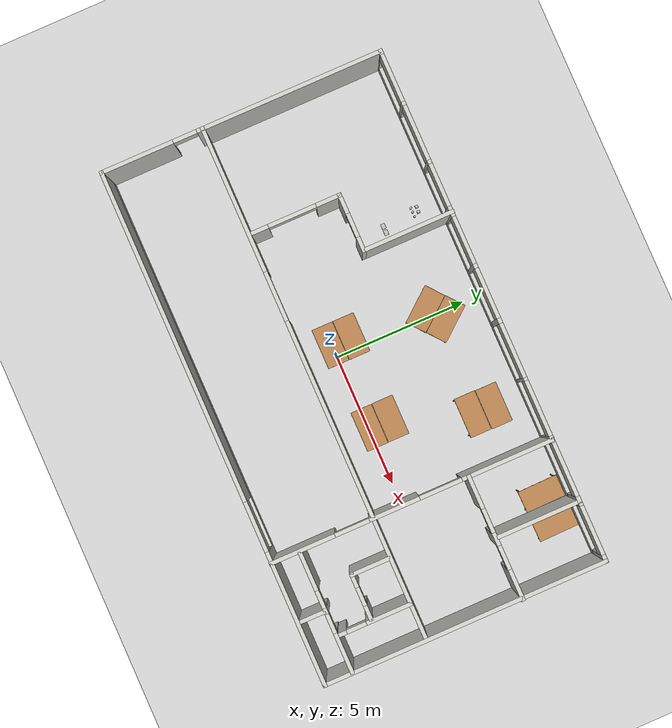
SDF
<sdf version="1.6">
 <world name="default">
  <light name="sun" type="directional">
   <pose>0 0 10 0 -0 0</pose>
   <diffuse>0.8 0.8 0.8 1</diffuse>
   <specular>0.2 0.2 0.2 1</specular>
   <attenuation>
    <range>1000</range>
    <constant>0.9</constant>
    <linear>0.01</linear>
    <quadratic>0.001</quadratic>
   </attenuation>
   <direction>-0.5 0.1 -0.9</direction>
  </light>
  <model name="ground_plane">
   <static>1</static>
   <link name="link">
    <collision name="collision">
     <geometry><plane><normal>0 0 1</normal><size>100 100</size></plane></geometry>
     <surface><friction><ode><mu>100</mu><mu2>50</mu2></ode></friction></surface>
    </collision>
    <visual name="visual">
     <cast_shadows>0</cast_shadows>
     <geometry><plane><normal>0 0 1</normal><size>100 100</size></plane></geometry>
     <material>
      <script><uri>file://media/materials/scripts/gazebo.material</uri><name>Gazebo/Grey</name></script>
     </material>
    </visual>
   </link>
  </model>
  <gravity>0 0 -9.8</gravity>
  <magnetic_field>6e-06 2.3e-05 -4.2e-05</magnetic_field>
  <atmosphere type="adiabatic"/>
  <physics name="default_physics" default="0" type="ode">
   <max_step_size>0.001</max_step_size>
   <real_time_factor>1</real_time_factor>
   <real_time_update_rate>1000</real_time_update_rate>
  </physics>
  <scene><ambient>0.4 0.4 0.4 1</ambient><background>0.7 0.7 0.7 1</background><shadows>1</shadows></scene>
  <spherical_coordinates>
   <surface_model>EARTH_WGS84</surface_model>
   <latitude_deg>0</latitude_deg>
   <longitude_deg>0</longitude_deg>
   <elevation>0</elevation>
   <heading_deg>0</heading_deg>
  </spherical_coordinates>
  <model name="spacious_building">
   <pose>0.613144 0.37216 0 0 -0 0</pose>
   <link name="Wall_0">
    <pose>-0.019346 5.3 0 0 -0 0</pose>
    <visual name="Wall_0_Visual_0">
     <pose>-9.64969 0 1.25 0 -0 0</pose>
     <geometry><box><size>0.200613 0.15 2.5</size></box></geometry>
     <material>
      <script><uri>file://media/materials/scripts/gazebo.material</uri><name>Gazebo/CeilingTiled</name></script>
      <ambient>0.215686 0.0196078 1 1</ambient>
     </material>
     <meta><layer>0</layer></meta>
    </visual>
    <collision name="Wall_0_Collision_0">
     <geometry><box><size>0.200613 0.15 2.5</size></box></geometry>
     <pose>-9.64969 0 1.25 0 -0 0</pose>
    </collision>
    <visual name="Wall_0_Visual_1">
     <pose>0.100307 0 0.25 0 -0 0</pose>
     <geometry><box><size>19.2994 0.15 0.5</size></box></geometry>
     <material>
      <script><uri>file://media/materials/scripts/gazebo.material</uri><name>Gazebo/CeilingTiled</name></script>
      <ambient>0.215686 0.0196078 1 1</ambient>
     </material>
     <meta><layer>0</layer></meta>
    </visual>
    <collision name="Wall_0_Collision_1">
     <geometry><box><size>19.2994 0.15 0.5</size></box></geometry>
     <pose>0.100307 0 0.25 0 -0 0</pose>
    </collision>
    <visual name="Wall_0_Visual_2">
     <pose>-7.66611 0 1.5 0 -0 0</pose>
     <geometry><box><size>0.146562 0.15 2</size></box></geometry>
     <material>
      <script><uri>file://media/materials/scripts/gazebo.material</uri><name>Gazebo/CeilingTiled</name></script>
      <ambient>0.215686 0.0196078 1 1</ambient>
     </material>
     <meta><layer>0</layer></meta>
    </visual>
    <collision name="Wall_0_Collision_2">
     <geometry><box><size>0.146562 0.15 2</size></box></geometry>
     <pose>-7.66611 0 1.5 0 -0 0</pose>
    </collision>
    <visual name="Wall_0_Visual_3">
     <pose>-5.44364 0 1.5 0 -0 0</pose>
     <geometry><box><size>0.144367 0.15 2</size></box></geometry>
     <material>
      <script><uri>file://media/materials/scripts/gazebo.material</uri><name>Gazebo/CeilingTiled</name></script>
      <ambient>0.215686 0.0196078 1 1</ambient>
     </material>
     <meta><layer>0</layer></meta>
    </visual>
    <collision name="Wall_0_Collision_3">
     <geometry><box><size>0.144367 0.15 2</size></box></geometry>
     <pose>-5.44364 0 1.5 0 -0 0</pose>
    </collision>
    <visual name="Wall_0_Visual_4">
     <pose>-3.5548 0 1.5 0 -0 0</pose>
     <geometry><box><size>0.389307 0.15 2</size></box></geometry>
     <material>
      <script><uri>file://media/materials/scripts/gazebo.material</uri><name>Gazebo/CeilingTiled</name></script>
      <ambient>0.215686 0.0196078 1 1</ambient>
     </material>
     <meta><layer>0</layer></meta>
    </visual>
    <collision name="Wall_0_Collision_4">
     <geometry><box><size>0.389307 0.15 2</size></box></geometry>
     <pose>-3.5548 0 1.5 0 -0 0</pose>
    </collision>
    <visual name="Wall_0_Visual_5">
     <pose>-1.48222 0 1.5 0 -0 0</pose>
     <geometry><box><size>0.161857 0.15 2</size></box></geometry>
     <material>
      <script><uri>file://media/materials/scripts/gazebo.material</uri><name>Gazebo/CeilingTiled</name></script>
      <ambient>0.215686 0.0196078 1 1</ambient>
     </material>
     <meta><layer>0</layer></meta>
    </visual>
    <collision name="Wall_0_Collision_5">
     <geometry><box><size>0.161857 0.15 2</size></box></geometry>
     <pose>-1.48222 0 1.5 0 -0 0</pose>
    </collision>
    <visual name="Wall_0_Visual_6">
     <pose>0.599214 0 1.5 0 -0 0</pose>
     <geometry><box><size>0.197013 0.15 2</size></box></geometry>
     <material>
      <script><uri>file://media/materials/scripts/gazebo.material</uri><name>Gazebo/CeilingTiled</name></script>
      <ambient>0.215686 0.0196078 1 1</ambient>
     </material>
     <meta><layer>0</layer></meta>
    </visual>
    <collision name="Wall_0_Collision_6">
     <geometry><box><size>0.197013 0.15 2</size></box></geometry>
     <pose>0.599214 0 1.5 0 -0 0</pose>
    </collision>
    <visual name="Wall_0_Visual_7">
     <pose>2.8116 0 1.5 0 -0 0</pose>
     <geometry><box><size>0.109758 0.15 2</size></box></geometry>
     <material>
      <script><uri>file://media/materials/scripts/gazebo.material</uri><name>Gazebo/CeilingTiled</name></script>
      <ambient>0.215686 0.0196078 1 1</ambient>
     </material>
     <meta><layer>0</layer></meta>
    </visual>
    <collision name="Wall_0_Collision_7">
     <geometry><box><size>0.109758 0.15 2</size></box></geometry>
     <pose>2.8116 0 1.5 0 -0 0</pose>
    </collision>
    <visual name="Wall_0_Visual_8">
     <pose>5.08532 0 1.5 0 -0 0</pose>
     <geometry><box><size>0.249688 0.15 2</size></box></geometry>
     <material>
      <script><uri>file://media/materials/scripts/gazebo.material</uri><name>Gazebo/CeilingTiled</name></script>
      <ambient>0.215686 0.0196078 1 1</ambient>
     </material>
     <meta><layer>0</layer></meta>
    </visual>
    <collision name="Wall_0_Collision_8">
     <geometry><box><size>0.249688 0.15 2</size></box></geometry>
     <pose>5.08532 0 1.5 0 -0 0</pose>
    </collision>
    <visual name="Wall_0_Visual_9">
     <pose>7.41151 0 1.5 0 -0 0</pose>
     <geometry><box><size>0.354698 0.15 2</size></box></geometry>
     <material>
      <script><uri>file://media/materials/scripts/gazebo.material</uri><name>Gazebo/CeilingTiled</name></script>
      <ambient>0.215686 0.0196078 1 1</ambient>
     </material>
     <meta><layer>0</layer></meta>
    </visual>
    <collision name="Wall_0_Collision_9">
     <geometry><box><size>0.354698 0.15 2</size></box></geometry>
     <pose>7.41151 0 1.5 0 -0 0</pose>
    </collision>
    <visual name="Wall_0_Visual_10">
     <pose>9.59393 0 1.5 0 -0 0</pose>
     <geometry><box><size>0.312136 0.15 2</size></box></geometry>
     <material>
      <script><uri>file://media/materials/scripts/gazebo.material</uri><name>Gazebo/CeilingTiled</name></script>
      <ambient>0.215686 0.0196078 1 1</ambient>
     </material>
     <meta><layer>0</layer></meta>
    </visual>
    <collision name="Wall_0_Collision_10">
     <geometry><box><size>0.312136 0.15 2</size></box></geometry>
     <pose>9.59393 0 1.5 0 -0 0</pose>
    </collision>
    <visual name="Wall_0_Visual_11">
     <pose>-8.64439 0 2.1 0 -0 0</pose>
     <geometry><box><size>1.81 0.15 0.8</size></box></geometry>
     <material>
      <script><uri>file://media/materials/scripts/gazebo.material</uri><name>Gazebo/CeilingTiled</name></script>
      <ambient>0.215686 0.0196078 1 1</ambient>
     </material>
     <meta><layer>0</layer></meta>
    </visual>
    <collision name="Wall_0_Collision_11">
     <geometry><box><size>1.81 0.15 0.8</size></box></geometry>
     <pose>-8.64439 0 2.1 0 -0 0</pose>
    </collision>
    <visual name="Wall_0_Visual_12">
     <pose>-6.55432 0 2.1 0 -0 0</pose>
     <geometry><box><size>2.077 0.15 0.8</size></box></geometry>
     <material>
      <script><uri>file://media/materials/scripts/gazebo.material</uri><name>Gazebo/CeilingTiled</name></script>
      <ambient>0.215686 0.0196078 1 1</ambient>
     </material>
     <meta><layer>0</layer></meta>
    </visual>
    <collision name="Wall_0_Collision_12">
     <geometry><box><size>2.077 0.15 0.8</size></box></geometry>
     <pose>-6.55432 0 2.1 0 -0 0</pose>
    </collision>
    <visual name="Wall_0_Visual_13">
     <pose>-4.56046 0 2.1 0 -0 0</pose>
     <geometry><box><size>1.622 0.15 0.8</size></box></geometry>
     <material>
      <script><uri>file://media/materials/scripts/gazebo.material</uri><name>Gazebo/CeilingTiled</name></script>
      <ambient>0.215686 0.0196078 1 1</ambient>
     </material>
     <meta><layer>0</layer></meta>
    </visual>
    <collision name="Wall_0_Collision_13">
     <geometry><box><size>1.622 0.15 0.8</size></box></geometry>
     <pose>-4.56046 0 2.1 0 -0 0</pose>
    </collision>
    <visual name="Wall_0_Visual_14">
     <pose>-2.46165 0 2.1 0 -0 0</pose>
     <geometry><box><size>1.797 0.15 0.8</size></box></geometry>
     <material>
      <script><uri>file://media/materials/scripts/gazebo.material</uri><name>Gazebo/CeilingTiled</name></script>
      <ambient>0.215686 0.0196078 1 1</ambient>
     </material>
     <meta><layer>0</layer></meta>
    </visual>
    <collision name="Wall_0_Collision_14">
     <geometry><box><size>1.797 0.15 0.8</size></box></geometry>
     <pose>-2.46165 0 2.1 0 -0 0</pose>
    </collision>
    <visual name="Wall_0_Visual_15">
     <pose>-0.450293 0 2.1 0 -0 0</pose>
     <geometry><box><size>1.902 0.15 0.8</size></box></geometry>
     <material>
      <script><uri>file://media/materials/scripts/gazebo.material</uri><name>Gazebo/CeilingTiled</name></script>
      <ambient>0.215686 0.0196078 1 1</ambient>
     </material>
     <meta><layer>0</layer></meta>
    </visual>
    <collision name="Wall_0_Collision_15">
     <geometry><box><size>1.902 0.15 0.8</size></box></geometry>
     <pose>-0.450293 0 2.1 0 -0 0</pose>
    </collision>
    <visual name="Wall_0_Visual_16">
     <pose>1.72722 0 2.1 0 -0 0</pose>
     <geometry><box><size>2.059 0.15 0.8</size></box></geometry>
     <material>
      <script><uri>file://media/materials/scripts/gazebo.material</uri><name>Gazebo/CeilingTiled</name></script>
      <ambient>0.215686 0.0196078 1 1</ambient>
     </material>
     <meta><layer>0</layer></meta>
    </visual>
    <collision name="Wall_0_Collision_16">
     <geometry><box><size>2.059 0.15 0.8</size></box></geometry>
     <pose>1.72722 0 2.1 0 -0 0</pose>
    </collision>
    <visual name="Wall_0_Visual_17">
     <pose>3.91348 0 2.1 0 -0 0</pose>
     <geometry><box><size>2.094 0.15 0.8</size></box></geometry>
     <material>
      <script><uri>file://media/materials/scripts/gazebo.material</uri><name>Gazebo/CeilingTiled</name></script>
      <ambient>0.215686 0.0196078 1 1</ambient>
     </material>
     <meta><layer>0</layer></meta>
    </visual>
    <collision name="Wall_0_Collision_17">
     <geometry><box><size>2.094 0.15 0.8</size></box></geometry>
     <pose>3.91348 0 2.1 0 -0 0</pose>
    </collision>
    <visual name="Wall_0_Visual_18">
     <pose>6.22217 0 2.1 0 -0 0</pose>
     <geometry><box><size>2.024 0.15 0.8</size></box></geometry>
     <material>
      <script><uri>file://media/materials/scripts/gazebo.material</uri><name>Gazebo/CeilingTiled</name></script>
      <ambient>0.215686 0.0196078 1 1</ambient>
     </material>
     <meta><layer>0</layer></meta>
    </visual>
    <collision name="Wall_0_Collision_18">
     <geometry><box><size>2.024 0.15 0.8</size></box></geometry>
     <pose>6.22217 0 2.1 0 -0 0</pose>
    </collision>
    <visual name="Wall_0_Visual_19">
     <pose>8.51336 0 2.1 0 -0 0</pose>
     <geometry><box><size>1.849 0.15 0.8</size></box></geometry>
     <material>
      <script><uri>file://media/materials/scripts/gazebo.material</uri><name>Gazebo/CeilingTiled</name></script>
      <ambient>0.215686 0.0196078 1 1</ambient>
     </material>
     <meta><layer>0</layer></meta>
    </visual>
    <collision name="Wall_0_Collision_19">
     <geometry><box><size>1.849 0.15 0.8</size></box></geometry>
     <pose>8.51336 0 2.1 0 -0 0</pose>
    </collision>
   </link>
   <link name="Wall_1">
    <collision name="Wall_1_Collision">
     <geometry><box><size>10.75 0.15 2.5</size></box></geometry>
     <pose>0 0 1.25 0 -0 0</pose>
    </collision>
    <visual name="Wall_1_Visual">
     <pose>0 0 1.25 0 -0 0</pose>
     <geometry><box><size>10.75 0.15 2.5</size></box></geometry>
     <material>
      <script><uri>file://media/materials/scripts/gazebo.material</uri><name>Gazebo/CeilingTiled</name></script>
      <ambient>1 0.431373 0.207843 1</ambient>
     </material>
     <meta><layer>0</layer></meta>
    </visual>
    <pose>9.65565 0 0 0 0 -1.5708</pose>
   </link>
   <link name="Wall_11">
    <pose>5.08476 -0.01749 0 0 0 -1.5708</pose>
    <visual name="Wall_11_Visual_0">
     <pose>-3.63755 0 1.25 0 -0 0</pose>
     <geometry><box><size>3.47489 0.15 2.5</size></box></geometry>
     <material>
      <script><uri>file://media/materials/scripts/gazebo.material</uri><name>Gazebo/CeilingTiled</name></script>
      <ambient>0.333333 0 0 1</ambient>
     </material>
     <meta><layer>0</layer></meta>
    </visual>
    <collision name="Wall_11_Collision_0">
     <geometry><box><size>3.47489 0.15 2.5</size></box></geometry>
     <pose>-3.63755 0 1.25 0 -0 0</pose>
    </collision>
    <visual name="Wall_11_Visual_1">
     <pose>0.648698 0 1.25 0 -0 0</pose>
     <geometry><box><size>1.89841 0.15 2.5</size></box></geometry>
     <material>
      <script><uri>file://media/materials/scripts/gazebo.material</uri><name>Gazebo/CeilingTiled</name></script>
      <ambient>0.333333 0 0 1</ambient>
     </material>
     <meta><layer>0</layer></meta>
    </visual>
    <collision name="Wall_11_Collision_1">
     <geometry><box><size>1.89841 0.15 2.5</size></box></geometry>
     <pose>0.648698 0 1.25 0 -0 0</pose>
    </collision>
    <visual name="Wall_11_Visual_2">
     <pose>4.13759 0 1.25 0 -0 0</pose>
     <geometry><box><size>2.47483 0.15 2.5</size></box></geometry>
     <material>
      <script><uri>file://media/materials/scripts/gazebo.material</uri><name>Gazebo/CeilingTiled</name></script>
      <ambient>0.333333 0 0 1</ambient>
     </material>
     <meta><layer>0</layer></meta>
    </visual>
    <collision name="Wall_11_Collision_2">
     <geometry><box><size>2.47483 0.15 2.5</size></box></geometry>
     <pose>4.13759 0 1.25 0 -0 0</pose>
    </collision>
    <visual name="Wall_11_Visual_3">
     <pose>-1.10031 0 2.25 0 -0 0</pose>
     <geometry><box><size>1.5996 0.15 0.5</size></box></geometry>
     <material>
      <script><uri>file://media/materials/scripts/gazebo.material</uri><name>Gazebo/CeilingTiled</name></script>
      <ambient>0.333333 0 0 1</ambient>
     </material>
     <meta><layer>0</layer></meta>
    </visual>
    <collision name="Wall_11_Collision_3">
     <geometry><box><size>1.5996 0.15 0.5</size></box></geometry>
     <pose>-1.10031 0 2.25 0 -0 0</pose>
    </collision>
    <visual name="Wall_11_Visual_4">
     <pose>2.24904 0 2.25 0 -0 0</pose>
     <geometry><box><size>1.30227 0.15 0.5</size></box></geometry>
     <material>
      <script><uri>file://media/materials/scripts/gazebo.material</uri><name>Gazebo/CeilingTiled</name></script>
      <ambient>0.333333 0 0 1</ambient>
     </material>
     <meta><layer>0</layer></meta>
    </visual>
    <collision name="Wall_11_Collision_4">
     <geometry><box><size>1.30227 0.15 0.5</size></box></geometry>
     <pose>2.24904 0 2.25 0 -0 0</pose>
    </collision>
   </link>
   <link name="Wall_15">
    <collision name="Wall_15_Collision">
     <geometry><box><size>3.25 0.15 2.5</size></box></geometry>
     <pose>0 0 1.25 0 -0 0</pose>
    </collision>
    <visual name="Wall_15_Visual">
     <pose>0 0 1.25 0 -0 0</pose>
     <geometry><box><size>3.25 0.15 2.5</size></box></geometry>
     <material>
      <script><uri>file://media/materials/scripts/gazebo.material</uri><name>Gazebo/CeilingTiled</name></script>
      <ambient>0 0.666667 1 1</ambient>
     </material>
     <meta><layer>0</layer></meta>
    </visual>
    <pose>7.40189 3.74021 0 0 0 -1.5708</pose>
   </link>
   <link name="Wall_17">
    <collision name="Wall_17_Collision">
     <geometry><box><size>1.6 0.15 2.5</size></box></geometry>
     <pose>0 0 1.25 0 -0 0</pose>
    </collision>
    <visual name="Wall_17_Visual">
     <pose>0 0 1.25 0 -0 0</pose>
     <geometry><box><size>1.6 0.15 2.5</size></box></geometry>
     <material>
      <script><uri>file://media/materials/scripts/gazebo.material</uri><name>Gazebo/CeilingTiled</name></script>
      <ambient>0.435294 0.796078 0.67451 1</ambient>
     </material>
     <meta><layer>0</layer></meta>
    </visual>
    <pose>6.55568 -2.20642 0 0 0 -1.5708</pose>
   </link>
   <link name="Wall_2">
    <pose>-0.019346 -5.3 0 0 -0 3.14159</pose>
    <visual name="Wall_2_Visual_0">
     <pose>-7.21529 0 1.25 0 -0 0</pose>
     <geometry><box><size>5.06942 0.15 2.5</size></box></geometry>
     <material>
      <script><uri>file://media/materials/scripts/gazebo.material</uri><name>Gazebo/CeilingTiled</name></script>
      <ambient>0.435294 0.796078 0.67451 1</ambient>
     </material>
     <meta><layer>0</layer></meta>
    </visual>
    <collision name="Wall_2_Collision_0">
     <geometry><box><size>5.06942 0.15 2.5</size></box></geometry>
     <pose>-7.21529 0 1.25 0 -0 0</pose>
    </collision>
    <visual name="Wall_2_Visual_1">
     <pose>2.53471 0 0.25 0 -0 0</pose>
     <geometry><box><size>14.4306 0.15 0.5</size></box></geometry>
     <material>
      <script><uri>file://media/materials/scripts/gazebo.material</uri><name>Gazebo/CeilingTiled</name></script>
      <ambient>0.435294 0.796078 0.67451 1</ambient>
     </material>
     <meta><layer>0</layer></meta>
    </visual>
    <collision name="Wall_2_Collision_1">
     <geometry><box><size>14.4306 0.15 0.5</size></box></geometry>
     <pose>2.53471 0 0.25 0 -0 0</pose>
    </collision>
    <visual name="Wall_2_Visual_2">
     <pose>3.47671 0 1.5 0 -0 0</pose>
     <geometry><box><size>12.5466 0.15 2</size></box></geometry>
     <material>
      <script><uri>file://media/materials/scripts/gazebo.material</uri><name>Gazebo/CeilingTiled</name></script>
      <ambient>0.435294 0.796078 0.67451 1</ambient>
     </material>
     <meta><layer>0</layer></meta>
    </visual>
    <collision name="Wall_2_Collision_2">
     <geometry><box><size>12.5466 0.15 2</size></box></geometry>
     <pose>3.47671 0 1.5 0 -0 0</pose>
    </collision>
    <visual name="Wall_2_Visual_3">
     <pose>-3.73858 0 2.1 0 -0 0</pose>
     <geometry><box><size>1.884 0.15 0.8</size></box></geometry>
     <material>
      <script><uri>file://media/materials/scripts/gazebo.material</uri><name>Gazebo/CeilingTiled</name></script>
      <ambient>0.435294 0.796078 0.67451 1</ambient>
     </material>
     <meta><layer>0</layer></meta>
    </visual>
    <collision name="Wall_2_Collision_3">
     <geometry><box><size>1.884 0.15 0.8</size></box></geometry>
     <pose>-3.73858 0 2.1 0 -0 0</pose>
    </collision>
   </link>
   <link name="Wall_20">
    <pose>8.28797 -2.83099 0 0 0 -1.5708</pose>
    <visual name="Wall_20_Visual_0">
     <pose>-0.558809 0 1.25 0 -0 0</pose>
     <geometry><box><size>1.73238 0.15 2.5</size></box></geometry>
     <material>
      <script><uri>file://media/materials/scripts/gazebo.material</uri><name>Gazebo/CeilingTiled</name></script>
      <ambient>0 0.666667 1 1</ambient>
     </material>
     <meta><layer>0</layer></meta>
    </visual>
    <collision name="Wall_20_Collision_0">
     <geometry><box><size>1.73238 0.15 2.5</size></box></geometry>
     <pose>-0.558809 0 1.25 0 -0 0</pose>
    </collision>
    <visual name="Wall_20_Visual_1">
     <pose>1.23615 0 1.25 0 -0 0</pose>
     <geometry><box><size>0.377709 0.15 2.5</size></box></geometry>
     <material>
      <script><uri>file://media/materials/scripts/gazebo.material</uri><name>Gazebo/CeilingTiled</name></script>
      <ambient>0 0.666667 1 1</ambient>
     </material>
     <meta><layer>0</layer></meta>
    </visual>
    <collision name="Wall_20_Collision_1">
     <geometry><box><size>0.377709 0.15 2.5</size></box></geometry>
     <pose>1.23615 0 1.25 0 -0 0</pose>
    </collision>
    <visual name="Wall_20_Visual_2">
     <pose>0.677336 0 2.25 0 -0 0</pose>
     <geometry><box><size>0.739909 0.15 0.5</size></box></geometry>
     <material>
      <script><uri>file://media/materials/scripts/gazebo.material</uri><name>Gazebo/CeilingTiled</name></script>
      <ambient>0 0.666667 1 1</ambient>
     </material>
     <meta><layer>0</layer></meta>
    </visual>
    <collision name="Wall_20_Collision_2">
     <geometry><box><size>0.739909 0.15 0.5</size></box></geometry>
     <pose>0.677336 0 2.25 0 -0 0</pose>
    </collision>
   </link>
   <link name="Wall_22">
    <pose>7.39869 -4.25824 0 0 -0 3.14159</pose>
    <visual name="Wall_22_Visual_0">
     <pose>-1.53589 0 1.25 0 -0 0</pose>
     <geometry><box><size>1.52823 0.15 2.5</size></box></geometry>
     <material>
      <script><uri>file://media/materials/scripts/gazebo.material</uri><name>Gazebo/CeilingTiled</name></script>
      <ambient>0.666667 0 1 1</ambient>
     </material>
     <meta><layer>0</layer></meta>
    </visual>
    <collision name="Wall_22_Collision_0">
     <geometry><box><size>1.52823 0.15 2.5</size></box></geometry>
     <pose>-1.53589 0 1.25 0 -0 0</pose>
    </collision>
    <visual name="Wall_22_Visual_1">
     <pose>0.058443 0 1.25 0 -0 0</pose>
     <geometry><box><size>0.214918 0.15 2.5</size></box></geometry>
     <material>
      <script><uri>file://media/materials/scripts/gazebo.material</uri><name>Gazebo/CeilingTiled</name></script>
      <ambient>0.666667 0 1 1</ambient>
     </material>
     <meta><layer>0</layer></meta>
    </visual>
    <collision name="Wall_22_Collision_1">
     <geometry><box><size>0.214918 0.15 2.5</size></box></geometry>
     <pose>0.058443 0 1.25 0 -0 0</pose>
    </collision>
    <visual name="Wall_22_Visual_2">
     <pose>1.56288 0 1.25 0 -0 0</pose>
     <geometry><box><size>1.47423 0.15 2.5</size></box></geometry>
     <material>
      <script><uri>file://media/materials/scripts/gazebo.material</uri><name>Gazebo/CeilingTiled</name></script>
      <ambient>0.666667 0 1 1</ambient>
     </material>
     <meta><layer>0</layer></meta>
    </visual>
    <collision name="Wall_22_Collision_2">
     <geometry><box><size>1.47423 0.15 2.5</size></box></geometry>
     <pose>1.56288 0 1.25 0 -0 0</pose>
    </collision>
    <visual name="Wall_22_Visual_3">
     <pose>-0.410395 0 2.25 0 -0 0</pose>
     <geometry><box><size>0.722756 0.15 0.5</size></box></geometry>
     <material>
      <script><uri>file://media/materials/scripts/gazebo.material</uri><name>Gazebo/CeilingTiled</name></script>
      <ambient>0.666667 0 1 1</ambient>
     </material>
     <meta><layer>0</layer></meta>
    </visual>
    <collision name="Wall_22_Collision_3">
     <geometry><box><size>0.722756 0.15 0.5</size></box></geometry>
     <pose>-0.410395 0 2.25 0 -0 0</pose>
    </collision>
    <visual name="Wall_22_Visual_4">
     <pose>0.495834 0 2.25 0 -0 0</pose>
     <geometry><box><size>0.659864 0.15 0.5</size></box></geometry>
     <material>
      <script><uri>file://media/materials/scripts/gazebo.material</uri><name>Gazebo/CeilingTiled</name></script>
      <ambient>0.666667 0 1 1</ambient>
     </material>
     <meta><layer>0</layer></meta>
    </visual>
    <collision name="Wall_22_Collision_4">
     <geometry><box><size>0.659864 0.15 0.5</size></box></geometry>
     <pose>0.495834 0 2.25 0 -0 0</pose>
    </collision>
   </link>
   <link name="Wall_24">
    <collision name="Wall_24_Collision">
     <geometry><box><size>1 0.15 2.5</size></box></geometry>
     <pose>0 0 1.25 0 -0 0</pose>
    </collision>
    <visual name="Wall_24_Visual">
     <pose>0 0 1.25 0 -0 0</pose>
     <geometry><box><size>1 0.15 2.5</size></box></geometry>
     <material>
      <script><uri>file://media/materials/scripts/gazebo.material</uri><name>Gazebo/CeilingTiled</name></script>
      <ambient>0.666667 0 1 1</ambient>
     </material>
     <meta><layer>0</layer></meta>
    </visual>
    <pose>7.33577 -4.76259 0 0 0 -1.5708</pose>
   </link>
   <link name="Wall_26">
    <pose>7.38068 -2.93142 0 0 -0 0</pose>
    <visual name="Wall_26_Visual_0">
     <pose>-0.62023 0 1.25 0 -0 0</pose>
     <geometry><box><size>0.559539 0.15 2.5</size></box></geometry>
     <material>
      <script><uri>file://media/materials/scripts/gazebo.material</uri><name>Gazebo/CeilingTiled</name></script>
      <ambient>0.921569 0.807843 0.615686 1</ambient>
     </material>
     <meta><layer>0</layer></meta>
    </visual>
    <collision name="Wall_26_Collision_0">
     <geometry><box><size>0.559539 0.15 2.5</size></box></geometry>
     <pose>-0.62023 0 1.25 0 -0 0</pose>
    </collision>
    <visual name="Wall_26_Visual_1">
     <pose>0.620035 0 1.25 0 -0 0</pose>
     <geometry><box><size>0.559929 0.15 2.5</size></box></geometry>
     <material>
      <script><uri>file://media/materials/scripts/gazebo.material</uri><name>Gazebo/CeilingTiled</name></script>
      <ambient>0.921569 0.807843 0.615686 1</ambient>
     </material>
     <meta><layer>0</layer></meta>
    </visual>
    <collision name="Wall_26_Collision_1">
     <geometry><box><size>0.559929 0.15 2.5</size></box></geometry>
     <pose>0.620035 0 1.25 0 -0 0</pose>
    </collision>
    <visual name="Wall_26_Visual_2">
     <pose>-0.000195 0 2.25 0 -0 0</pose>
     <geometry><box><size>0.680531 0.15 0.5</size></box></geometry>
     <material>
      <script><uri>file://media/materials/scripts/gazebo.material</uri><name>Gazebo/CeilingTiled</name></script>
      <ambient>0.921569 0.807843 0.615686 1</ambient>
     </material>
     <meta><layer>0</layer></meta>
    </visual>
    <collision name="Wall_26_Collision_2">
     <geometry><box><size>0.680531 0.15 0.5</size></box></geometry>
     <pose>-0.000195 0 2.25 0 -0 0</pose>
    </collision>
   </link>
   <link name="Wall_28">
    <pose>7.39435 2.14097 0 0 -0 0</pose>
    <visual name="Wall_28_Visual_0">
     <pose>-1.73172 0 1.25 0 -0 0</pose>
     <geometry><box><size>1.28656 0.15 2.5</size></box></geometry>
     <material>
      <script><uri>file://media/materials/scripts/gazebo.material</uri><name>Gazebo/CeilingTiled</name></script>
      <ambient>0.333333 0.666667 0.498039 1</ambient>
     </material>
     <meta><layer>0</layer></meta>
    </visual>
    <collision name="Wall_28_Collision_0">
     <geometry><box><size>1.28656 0.15 2.5</size></box></geometry>
     <pose>-1.73172 0 1.25 0 -0 0</pose>
    </collision>
    <visual name="Wall_28_Visual_1">
     <pose>0.052413 0 1.25 0 -0 0</pose>
     <geometry><box><size>0.481714 0.15 2.5</size></box></geometry>
     <material>
      <script><uri>file://media/materials/scripts/gazebo.material</uri><name>Gazebo/CeilingTiled</name></script>
      <ambient>0.333333 0.666667 0.498039 1</ambient>
     </material>
     <meta><layer>0</layer></meta>
    </visual>
    <collision name="Wall_28_Collision_1">
     <geometry><box><size>0.481714 0.15 2.5</size></box></geometry>
     <pose>0.052413 0 1.25 0 -0 0</pose>
    </collision>
    <visual name="Wall_28_Visual_2">
     <pose>1.78414 0 1.25 0 -0 0</pose>
     <geometry><box><size>1.18173 0.15 2.5</size></box></geometry>
     <material>
      <script><uri>file://media/materials/scripts/gazebo.material</uri><name>Gazebo/CeilingTiled</name></script>
      <ambient>0.333333 0.666667 0.498039 1</ambient>
     </material>
     <meta><layer>0</layer></meta>
    </visual>
    <collision name="Wall_28_Collision_2">
     <geometry><box><size>1.18173 0.15 2.5</size></box></geometry>
     <pose>1.78414 0 1.25 0 -0 0</pose>
    </collision>
    <visual name="Wall_28_Visual_3">
     <pose>-0.638444 0 2.25 0 -0 0</pose>
     <geometry><box><size>0.9 0.15 0.5</size></box></geometry>
     <material>
      <script><uri>file://media/materials/scripts/gazebo.material</uri><name>Gazebo/CeilingTiled</name></script>
      <ambient>0.333333 0.666667 0.498039 1</ambient>
     </material>
     <meta><layer>0</layer></meta>
    </visual>
    <collision name="Wall_28_Collision_3">
     <geometry><box><size>0.9 0.15 0.5</size></box></geometry>
     <pose>-0.638444 0 2.25 0 -0 0</pose>
    </collision>
    <visual name="Wall_28_Visual_4">
     <pose>0.74327 0 2.25 0 -0 0</pose>
     <geometry><box><size>0.9 0.15 0.5</size></box></geometry>
     <material>
      <script><uri>file://media/materials/scripts/gazebo.material</uri><name>Gazebo/CeilingTiled</name></script>
      <ambient>0.333333 0.666667 0.498039 1</ambient>
     </material>
     <meta><layer>0</layer></meta>
    </visual>
    <collision name="Wall_28_Collision_4">
     <geometry><box><size>0.9 0.15 0.5</size></box></geometry>
     <pose>0.74327 0 2.25 0 -0 0</pose>
    </collision>
   </link>
   <link name="Wall_3">
    <pose>-9.69435 0 0 0 -0 1.5708</pose>
    <visual name="Wall_3_Visual_0">
     <pose>-3.98455 0 1.25 0 -0 0</pose>
     <geometry><box><size>2.7809 0.15 2.5</size></box></geometry>
     <material>
      <script><uri>file://media/materials/scripts/gazebo.material</uri><name>Gazebo/CeilingTiled</name></script>
      <ambient>0.333333 0.666667 0.498039 1</ambient>
     </material>
     <meta><layer>0</layer></meta>
    </visual>
    <collision name="Wall_3_Collision_0">
     <geometry><box><size>2.7809 0.15 2.5</size></box></geometry>
     <pose>-3.98455 0 1.25 0 -0 0</pose>
    </collision>
    <visual name="Wall_3_Visual_1">
     <pose>1.84045 0 1.25 0 -0 0</pose>
     <geometry><box><size>7.0691 0.15 2.5</size></box></geometry>
     <material>
      <script><uri>file://media/materials/scripts/gazebo.material</uri><name>Gazebo/CeilingTiled</name></script>
      <ambient>0.333333 0.666667 0.498039 1</ambient>
     </material>
     <meta><layer>0</layer></meta>
    </visual>
    <collision name="Wall_3_Collision_1">
     <geometry><box><size>7.0691 0.15 2.5</size></box></geometry>
     <pose>1.84045 0 1.25 0 -0 0</pose>
    </collision>
    <visual name="Wall_3_Visual_2">
     <pose>-2.1441 0 2.25 0 -0 0</pose>
     <geometry><box><size>0.9 0.15 0.5</size></box></geometry>
     <material>
      <script><uri>file://media/materials/scripts/gazebo.material</uri><name>Gazebo/CeilingTiled</name></script>
      <ambient>0.333333 0.666667 0.498039 1</ambient>
     </material>
     <meta><layer>0</layer></meta>
    </visual>
    <collision name="Wall_3_Collision_2">
     <geometry><box><size>0.9 0.15 0.5</size></box></geometry>
     <pose>-2.1441 0 2.25 0 -0 0</pose>
    </collision>
   </link>
   <link name="Wall_5">
    <collision name="Wall_5_Collision">
     <geometry><box><size>3.5 0.15 2.5</size></box></geometry>
     <pose>0 0 1.25 0 -0 0</pose>
    </collision>
    <visual name="Wall_5_Visual">
     <pose>0 0 1.25 0 -0 0</pose>
     <geometry><box><size>3.5 0.15 2.5</size></box></geometry>
     <material>
      <script><uri>file://media/materials/scripts/gazebo.material</uri><name>Gazebo/CeilingTiled</name></script>
      <ambient>0 0.666667 1 1</ambient>
     </material>
     <meta><layer>0</layer></meta>
    </visual>
    <pose>-3.55533 3.64249 0 0 0 -1.5708</pose>
   </link>
   <link name="Wall_6">
    <pose>-4.60533 1.96749 0 0 -0 3.14159</pose>
    <visual name="Wall_6_Visual_0">
     <pose>-0.836318 0 1.25 0 -0 0</pose>
     <geometry><box><size>0.577364 0.15 2.5</size></box></geometry>
     <material>
      <script><uri>file://media/materials/scripts/gazebo.material</uri><name>Gazebo/CeilingTiled</name></script>
      <ambient>0.666667 1 0.498039 1</ambient>
     </material>
     <meta><layer>0</layer></meta>
    </visual>
    <collision name="Wall_6_Collision_0">
     <geometry><box><size>0.577364 0.15 2.5</size></box></geometry>
     <pose>-0.836318 0 1.25 0 -0 0</pose>
    </collision>
    <visual name="Wall_6_Visual_1">
     <pose>0.738682 0 1.25 0 -0 0</pose>
     <geometry><box><size>0.772636 0.15 2.5</size></box></geometry>
     <material>
      <script><uri>file://media/materials/scripts/gazebo.material</uri><name>Gazebo/CeilingTiled</name></script>
      <ambient>0.666667 1 0.498039 1</ambient>
     </material>
     <meta><layer>0</layer></meta>
    </visual>
    <collision name="Wall_6_Collision_1">
     <geometry><box><size>0.772636 0.15 2.5</size></box></geometry>
     <pose>0.738682 0 1.25 0 -0 0</pose>
    </collision>
    <visual name="Wall_6_Visual_2">
     <pose>-0.097636 0 2.25 0 -0 0</pose>
     <geometry><box><size>0.9 0.15 0.5</size></box></geometry>
     <material>
      <script><uri>file://media/materials/scripts/gazebo.material</uri><name>Gazebo/CeilingTiled</name></script>
      <ambient>0.666667 1 0.498039 1</ambient>
     </material>
     <meta><layer>0</layer></meta>
    </visual>
    <collision name="Wall_6_Collision_2">
     <geometry><box><size>0.9 0.15 0.5</size></box></geometry>
     <pose>-0.097636 0 2.25 0 -0 0</pose>
    </collision>
   </link>
   <link name="Wall_7">
    <pose>-5.65533 0.29249 0 0 0 -1.5708</pose>
    <visual name="Wall_7_Visual_0">
     <pose>-1.26342 0 1.25 0 -0 0</pose>
     <geometry><box><size>0.973159 0.15 2.5</size></box></geometry>
     <material>
      <script><uri>file://media/materials/scripts/gazebo.material</uri><name>Gazebo/CeilingTiled</name></script>
      <ambient>1 1 0.498039 1</ambient>
     </material>
     <meta><layer>0</layer></meta>
    </visual>
    <collision name="Wall_7_Collision_0">
     <geometry><box><size>0.973159 0.15 2.5</size></box></geometry>
     <pose>-1.26342 0 1.25 0 -0 0</pose>
    </collision>
    <visual name="Wall_7_Visual_1">
     <pose>1.39132 0 1.25 0 -0 0</pose>
     <geometry><box><size>0.717358 0.15 2.5</size></box></geometry>
     <material>
      <script><uri>file://media/materials/scripts/gazebo.material</uri><name>Gazebo/CeilingTiled</name></script>
      <ambient>1 1 0.498039 1</ambient>
     </material>
     <meta><layer>0</layer></meta>
    </visual>
    <collision name="Wall_7_Collision_1">
     <geometry><box><size>0.717358 0.15 2.5</size></box></geometry>
     <pose>1.39132 0 1.25 0 -0 0</pose>
    </collision>
    <visual name="Wall_7_Visual_2">
     <pose>0.1279 0 2.25 0 -0 0</pose>
     <geometry><box><size>1.80948 0.15 0.5</size></box></geometry>
     <material>
      <script><uri>file://media/materials/scripts/gazebo.material</uri><name>Gazebo/CeilingTiled</name></script>
      <ambient>1 1 0.498039 1</ambient>
     </material>
     <meta><layer>0</layer></meta>
    </visual>
    <collision name="Wall_7_Collision_2">
     <geometry><box><size>1.80948 0.15 0.5</size></box></geometry>
     <pose>0.1279 0 2.25 0 -0 0</pose>
    </collision>
   </link>
   <link name="Wall_9">
    <pose>-0.019346 -1.46865 0 0 -0 0</pose>
    <visual name="Wall_9_Visual_0">
     <pose>-6.98563 0 1.25 0 -0 0</pose>
     <geometry><box><size>5.52874 0.15 2.5</size></box></geometry>
     <material>
      <script><uri>file://media/materials/scripts/gazebo.material</uri><name>Gazebo/CeilingTiled</name></script>
      <ambient>0.996078 0.47451 0.0196078 1</ambient>
     </material>
     <meta><layer>0</layer></meta>
    </visual>
    <collision name="Wall_9_Collision_0">
     <geometry><box><size>5.52874 0.15 2.5</size></box></geometry>
     <pose>-6.98563 0 1.25 0 -0 0</pose>
    </collision>
    <visual name="Wall_9_Visual_1">
     <pose>3.69535 0 1.25 0 -0 0</pose>
     <geometry><box><size>12.1093 0.15 2.5</size></box></geometry>
     <material>
      <script><uri>file://media/materials/scripts/gazebo.material</uri><name>Gazebo/CeilingTiled</name></script>
      <ambient>0.996078 0.47451 0.0196078 1</ambient>
     </material>
     <meta><layer>0</layer></meta>
    </visual>
    <collision name="Wall_9_Collision_1">
     <geometry><box><size>12.1093 0.15 2.5</size></box></geometry>
     <pose>3.69535 0 1.25 0 -0 0</pose>
    </collision>
    <visual name="Wall_9_Visual_2">
     <pose>-3.29028 0 2.25 0 -0 0</pose>
     <geometry><box><size>1.86195 0.15 0.5</size></box></geometry>
     <material>
      <script><uri>file://media/materials/scripts/gazebo.material</uri><name>Gazebo/CeilingTiled</name></script>
      <ambient>0.996078 0.47451 0.0196078 1</ambient>
     </material>
     <meta><layer>0</layer></meta>
    </visual>
    <collision name="Wall_9_Collision_2">
     <geometry><box><size>1.86195 0.15 0.5</size></box></geometry>
     <pose>-3.29028 0 2.25 0 -0 0</pose>
    </collision>
   </link>
   <static>1</static>
  </model>
  <model name="table">
   <static>1</static>
   <link name="link">
    <collision name="surface">
     <pose>0 0 1 0 -0 0</pose>
     <geometry><box><size>1.5 0.8 0.03</size></box></geometry>
     <surface><friction><ode><mu>0.6</mu><mu2>0.6</mu2></ode></friction></surface>
    </collision>
    <visual name="visual1">
     <pose>0 0 1 0 -0 0</pose>
     <geometry><box><size>1.5 0.8 0.03</size></box></geometry>
     <material>
      <script><uri>file://media/materials/scripts/gazebo.material</uri><name>Gazebo/Wood</name></script>
     </material>
    </visual>
    <collision name="front_left_leg">
     <pose>0.68 0.38 0.5 0 -0 0</pose>
     <geometry><cylinder><radius>0.02</radius><length>1</length></cylinder></geometry>
    </collision>
    <visual name="front_left_leg">
     <pose>0.68 0.38 0.5 0 -0 0</pose>
     <geometry><cylinder><radius>0.02</radius><length>1</length></cylinder></geometry>
     <material>
      <script><uri>file://media/materials/scripts/gazebo.material</uri><name>Gazebo/Grey</name></script>
     </material>
    </visual>
    <collision name="front_right_leg">
     <pose>0.68 -0.38 0.5 0 -0 0</pose>
     <geometry><cylinder><radius>0.02</radius><length>1</length></cylinder></geometry>
    </collision>
    <visual name="front_right_leg">
     <pose>0.68 -0.38 0.5 0 -0 0</pose>
     <geometry><cylinder><radius>0.02</radius><length>1</length></cylinder></geometry>
     <material>
      <script><uri>file://media/materials/scripts/gazebo.material</uri><name>Gazebo/Grey</name></script>
     </material>
    </visual>
    <collision name="back_right_leg">
     <pose>-0.68 -0.38 0.5 0 -0 0</pose>
     <geometry><cylinder><radius>0.02</radius><length>1</length></cylinder></geometry>
    </collision>
    <visual name="back_right_leg">
     <pose>-0.68 -0.38 0.5 0 -0 0</pose>
     <geometry><cylinder><radius>0.02</radius><length>1</length></cylinder></geometry>
     <material>
      <script><uri>file://media/materials/scripts/gazebo.material</uri><name>Gazebo/Grey</name></script>
     </material>
    </visual>
    <collision name="back_left_leg">
     <pose>-0.68 0.38 0.5 0 -0 0</pose>
     <geometry><cylinder><radius>0.02</radius><length>1</length></cylinder></geometry>
    </collision>
    <visual name="back_left_leg">
     <pose>-0.68 0.38 0.5 0 -0 0</pose>
     <geometry><cylinder><radius>0.02</radius><length>1</length></cylinder></geometry>
     <material>
      <script><uri>file://media/materials/scripts/gazebo.material</uri><name>Gazebo/Grey</name></script>
     </material>
    </visual>
   </link>
   <pose>-0.454136 -0.043466 0 0 -0 0</pose>
  </model>
  <model name="table_0">
   <static>1</static>
   <link name="link">
    <collision name="surface">
     <pose>0 0 1 0 -0 0</pose>
     <geometry><box><size>1.5 0.8 0.03</size></box></geometry>
     <surface><friction><ode><mu>0.6</mu><mu2>0.6</mu2></ode></friction></surface>
    </collision>
    <visual name="visual1">
     <pose>0 0 1 0 -0 0</pose>
     <geometry><box><size>1.5 0.8 0.03</size></box></geometry>
     <material>
      <script><uri>file://media/materials/scripts/gazebo.material</uri><name>Gazebo/Wood</name></script>
     </material>
    </visual>
    <collision name="front_left_leg">
     <pose>0.68 0.38 0.5 0 -0 0</pose>
     <geometry><cylinder><radius>0.02</radius><length>1</length></cylinder></geometry>
    </collision>
    <visual name="front_left_leg">
     <pose>0.68 0.38 0.5 0 -0 0</pose>
     <geometry><cylinder><radius>0.02</radius><length>1</length></cylinder></geometry>
     <material>
      <script><uri>file://media/materials/scripts/gazebo.material</uri><name>Gazebo/Grey</name></script>
     </material>
    </visual>
    <collision name="front_right_leg">
     <pose>0.68 -0.38 0.5 0 -0 0</pose>
     <geometry><cylinder><radius>0.02</radius><length>1</length></cylinder></geometry>
    </collision>
    <visual name="front_right_leg">
     <pose>0.68 -0.38 0.5 0 -0 0</pose>
     <geometry><cylinder><radius>0.02</radius><length>1</length></cylinder></geometry>
     <material>
      <script><uri>file://media/materials/scripts/gazebo.material</uri><name>Gazebo/Grey</name></script>
     </material>
    </visual>
    <collision name="back_right_leg">
     <pose>-0.68 -0.38 0.5 0 -0 0</pose>
     <geometry><cylinder><radius>0.02</radius><length>1</length></cylinder></geometry>
    </collision>
    <visual name="back_right_leg">
     <pose>-0.68 -0.38 0.5 0 -0 0</pose>
     <geometry><cylinder><radius>0.02</radius><length>1</length></cylinder></geometry>
     <material>
      <script><uri>file://media/materials/scripts/gazebo.material</uri><name>Gazebo/Grey</name></script>
     </material>
    </visual>
    <collision name="back_left_leg">
     <pose>-0.68 0.38 0.5 0 -0 0</pose>
     <geometry><cylinder><radius>0.02</radius><length>1</length></cylinder></geometry>
    </collision>
    <visual name="back_left_leg">
     <pose>-0.68 0.38 0.5 0 -0 0</pose>
     <geometry><cylinder><radius>0.02</radius><length>1</length></cylinder></geometry>
     <material>
      <script><uri>file://media/materials/scripts/gazebo.material</uri><name>Gazebo/Grey</name></script>
     </material>
    </visual>
   </link>
   <pose>-0.451822 0.770435 0 0 -0 0</pose>
  </model>
  <model name="table_1">
   <static>1</static>
   <link name="link">
    <collision name="surface">
     <pose>0 0 1 0 -0 0</pose>
     <geometry><box><size>1.5 0.8 0.03</size></box></geometry>
     <surface><friction><ode><mu>0.6</mu><mu2>0.6</mu2></ode></friction></surface>
    </collision>
    <visual name="visual1">
     <pose>0 0 1 0 -0 0</pose>
     <geometry><box><size>1.5 0.8 0.03</size></box></geometry>
     <material>
      <script><uri>file://media/materials/scripts/gazebo.material</uri><name>Gazebo/Wood</name></script>
     </material>
    </visual>
    <collision name="front_left_leg">
     <pose>0.68 0.38 0.5 0 -0 0</pose>
     <geometry><cylinder><radius>0.02</radius><length>1</length></cylinder></geometry>
    </collision>
    <visual name="front_left_leg">
     <pose>0.68 0.38 0.5 0 -0 0</pose>
     <geometry><cylinder><radius>0.02</radius><length>1</length></cylinder></geometry>
     <material>
      <script><uri>file://media/materials/scripts/gazebo.material</uri><name>Gazebo/Grey</name></script>
     </material>
    </visual>
    <collision name="front_right_leg">
     <pose>0.68 -0.38 0.5 0 -0 0</pose>
     <geometry><cylinder><radius>0.02</radius><length>1</length></cylinder></geometry>
    </collision>
    <visual name="front_right_leg">
     <pose>0.68 -0.38 0.5 0 -0 0</pose>
     <geometry><cylinder><radius>0.02</radius><length>1</length></cylinder></geometry>
     <material>
      <script><uri>file://media/materials/scripts/gazebo.material</uri><name>Gazebo/Grey</name></script>
     </material>
    </visual>
    <collision name="back_right_leg">
     <pose>-0.68 -0.38 0.5 0 -0 0</pose>
     <geometry><cylinder><radius>0.02</radius><length>1</length></cylinder></geometry>
    </collision>
    <visual name="back_right_leg">
     <pose>-0.68 -0.38 0.5 0 -0 0</pose>
     <geometry><cylinder><radius>0.02</radius><length>1</length></cylinder></geometry>
     <material>
      <script><uri>file://media/materials/scripts/gazebo.material</uri><name>Gazebo/Grey</name></script>
     </material>
    </visual>
    <collision name="back_left_leg">
     <pose>-0.68 0.38 0.5 0 -0 0</pose>
     <geometry><cylinder><radius>0.02</radius><length>1</length></cylinder></geometry>
    </collision>
    <visual name="back_left_leg">
     <pose>-0.68 0.38 0.5 0 -0 0</pose>
     <geometry><cylinder><radius>0.02</radius><length>1</length></cylinder></geometry>
     <material>
      <script><uri>file://media/materials/scripts/gazebo.material</uri><name>Gazebo/Grey</name></script>
     </material>
    </visual>
   </link>
   <pose>2.80382 0.047046 0 0 -0 0</pose>
  </model>
  <model name="table_2">
   <static>1</static>
   <link name="link">
    <collision name="surface">
     <pose>0 0 1 0 -0 0</pose>
     <geometry><box><size>1.5 0.8 0.03</size></box></geometry>
     <surface><friction><ode><mu>0.6</mu><mu2>0.6</mu2></ode></friction></surface>
    </collision>
    <visual name="visual1">
     <pose>0 0 1 0 -0 0</pose>
     <geometry><box><size>1.5 0.8 0.03</size></box></geometry>
     <material>
      <script><uri>file://media/materials/scripts/gazebo.material</uri><name>Gazebo/Wood</name></script>
     </material>
    </visual>
    <collision name="front_left_leg">
     <pose>0.68 0.38 0.5 0 -0 0</pose>
     <geometry><cylinder><radius>0.02</radius><length>1</length></cylinder></geometry>
    </collision>
    <visual name="front_left_leg">
     <pose>0.68 0.38 0.5 0 -0 0</pose>
     <geometry><cylinder><radius>0.02</radius><length>1</length></cylinder></geometry>
     <material>
      <script><uri>file://media/materials/scripts/gazebo.material</uri><name>Gazebo/Grey</name></script>
     </material>
    </visual>
    <collision name="front_right_leg">
     <pose>0.68 -0.38 0.5 0 -0 0</pose>
     <geometry><cylinder><radius>0.02</radius><length>1</length></cylinder></geometry>
    </collision>
    <visual name="front_right_leg">
     <pose>0.68 -0.38 0.5 0 -0 0</pose>
     <geometry><cylinder><radius>0.02</radius><length>1</length></cylinder></geometry>
     <material>
      <script><uri>file://media/materials/scripts/gazebo.material</uri><name>Gazebo/Grey</name></script>
     </material>
    </visual>
    <collision name="back_right_leg">
     <pose>-0.68 -0.38 0.5 0 -0 0</pose>
     <geometry><cylinder><radius>0.02</radius><length>1</length></cylinder></geometry>
    </collision>
    <visual name="back_right_leg">
     <pose>-0.68 -0.38 0.5 0 -0 0</pose>
     <geometry><cylinder><radius>0.02</radius><length>1</length></cylinder></geometry>
     <material>
      <script><uri>file://media/materials/scripts/gazebo.material</uri><name>Gazebo/Grey</name></script>
     </material>
    </visual>
    <collision name="back_left_leg">
     <pose>-0.68 0.38 0.5 0 -0 0</pose>
     <geometry><cylinder><radius>0.02</radius><length>1</length></cylinder></geometry>
    </collision>
    <visual name="back_left_leg">
     <pose>-0.68 0.38 0.5 0 -0 0</pose>
     <geometry><cylinder><radius>0.02</radius><length>1</length></cylinder></geometry>
     <material>
      <script><uri>file://media/materials/scripts/gazebo.material</uri><name>Gazebo/Grey</name></script>
     </material>
    </visual>
   </link>
   <pose>2.79953 0.861475 0 0 -0 0</pose>
  </model>
  <model name="table_3">
   <static>1</static>
   <link name="link">
    <collision name="surface">
     <pose>0 0 1 0 -0 0</pose>
     <geometry><box><size>1.5 0.8 0.03</size></box></geometry>
     <surface><friction><ode><mu>0.6</mu><mu2>0.6</mu2></ode></friction></surface>
    </collision>
    <visual name="visual1">
     <pose>0 0 1 0 -0 0</pose>
     <geometry><box><size>1.5 0.8 0.03</size></box></geometry>
     <material>
      <script><uri>file://media/materials/scripts/gazebo.material</uri><name>Gazebo/Wood</name></script>
     </material>
    </visual>
    <collision name="front_left_leg">
     <pose>0.68 0.38 0.5 0 -0 0</pose>
     <geometry><cylinder><radius>0.02</radius><length>1</length></cylinder></geometry>
    </collision>
    <visual name="front_left_leg">
     <pose>0.68 0.38 0.5 0 -0 0</pose>
     <geometry><cylinder><radius>0.02</radius><length>1</length></cylinder></geometry>
     <material>
      <script><uri>file://media/materials/scripts/gazebo.material</uri><name>Gazebo/Grey</name></script>
     </material>
    </visual>
    <collision name="front_right_leg">
     <pose>0.68 -0.38 0.5 0 -0 0</pose>
     <geometry><cylinder><radius>0.02</radius><length>1</length></cylinder></geometry>
    </collision>
    <visual name="front_right_leg">
     <pose>0.68 -0.38 0.5 0 -0 0</pose>
     <geometry><cylinder><radius>0.02</radius><length>1</length></cylinder></geometry>
     <material>
      <script><uri>file://media/materials/scripts/gazebo.material</uri><name>Gazebo/Grey</name></script>
     </material>
    </visual>
    <collision name="back_right_leg">
     <pose>-0.68 -0.38 0.5 0 -0 0</pose>
     <geometry><cylinder><radius>0.02</radius><length>1</length></cylinder></geometry>
    </collision>
    <visual name="back_right_leg">
     <pose>-0.68 -0.38 0.5 0 -0 0</pose>
     <geometry><cylinder><radius>0.02</radius><length>1</length></cylinder></geometry>
     <material>
      <script><uri>file://media/materials/scripts/gazebo.material</uri><name>Gazebo/Grey</name></script>
     </material>
    </visual>
    <collision name="back_left_leg">
     <pose>-0.68 0.38 0.5 0 -0 0</pose>
     <geometry><cylinder><radius>0.02</radius><length>1</length></cylinder></geometry>
    </collision>
    <visual name="back_left_leg">
     <pose>-0.68 0.38 0.5 0 -0 0</pose>
     <geometry><cylinder><radius>0.02</radius><length>1</length></cylinder></geometry>
     <material>
      <script><uri>file://media/materials/scripts/gazebo.material</uri><name>Gazebo/Grey</name></script>
     </material>
    </visual>
   </link>
   <pose>3.85462 4.42765 0 0 -0 0</pose>
  </model>
  <model name="table_4">
   <static>1</static>
   <link name="link">
    <collision name="surface">
     <pose>0 0 1 0 -0 0</pose>
     <geometry><box><size>1.5 0.8 0.03</size></box></geometry>
     <surface><friction><ode><mu>0.6</mu><mu2>0.6</mu2></ode></friction></surface>
    </collision>
    <visual name="visual1">
     <pose>0 0 1 0 -0 0</pose>
     <geometry><box><size>1.5 0.8 0.03</size></box></geometry>
     <material>
      <script><uri>file://media/materials/scripts/gazebo.material</uri><name>Gazebo/Wood</name></script>
     </material>
    </visual>
    <collision name="front_left_leg">
     <pose>0.68 0.38 0.5 0 -0 0</pose>
     <geometry><cylinder><radius>0.02</radius><length>1</length></cylinder></geometry>
    </collision>
    <visual name="front_left_leg">
     <pose>0.68 0.38 0.5 0 -0 0</pose>
     <geometry><cylinder><radius>0.02</radius><length>1</length></cylinder></geometry>
     <material>
      <script><uri>file://media/materials/scripts/gazebo.material</uri><name>Gazebo/Grey</name></script>
     </material>
    </visual>
    <collision name="front_right_leg">
     <pose>0.68 -0.38 0.5 0 -0 0</pose>
     <geometry><cylinder><radius>0.02</radius><length>1</length></cylinder></geometry>
    </collision>
    <visual name="front_right_leg">
     <pose>0.68 -0.38 0.5 0 -0 0</pose>
     <geometry><cylinder><radius>0.02</radius><length>1</length></cylinder></geometry>
     <material>
      <script><uri>file://media/materials/scripts/gazebo.material</uri><name>Gazebo/Grey</name></script>
     </material>
    </visual>
    <collision name="back_right_leg">
     <pose>-0.68 -0.38 0.5 0 -0 0</pose>
     <geometry><cylinder><radius>0.02</radius><length>1</length></cylinder></geometry>
    </collision>
    <visual name="back_right_leg">
     <pose>-0.68 -0.38 0.5 0 -0 0</pose>
     <geometry><cylinder><radius>0.02</radius><length>1</length></cylinder></geometry>
     <material>
      <script><uri>file://media/materials/scripts/gazebo.material</uri><name>Gazebo/Grey</name></script>
     </material>
    </visual>
    <collision name="back_left_leg">
     <pose>-0.68 0.38 0.5 0 -0 0</pose>
     <geometry><cylinder><radius>0.02</radius><length>1</length></cylinder></geometry>
    </collision>
    <visual name="back_left_leg">
     <pose>-0.68 0.38 0.5 0 -0 0</pose>
     <geometry><cylinder><radius>0.02</radius><length>1</length></cylinder></geometry>
     <material>
      <script><uri>file://media/materials/scripts/gazebo.material</uri><name>Gazebo/Grey</name></script>
     </material>
    </visual>
   </link>
   <pose>3.83821 3.6155 0 0 -0 0</pose>
  </model>
  <model name="table_5">
   <static>1</static>
   <link name="link">
    <collision name="surface">
     <pose>0 0 1 0 -0 0</pose>
     <geometry><box><size>1.5 0.8 0.03</size></box></geometry>
     <surface><friction><ode><mu>0.6</mu><mu2>0.6</mu2></ode></friction></surface>
    </collision>
    <visual name="visual1">
     <pose>0 0 1 0 -0 0</pose>
     <geometry><box><size>1.5 0.8 0.03</size></box></geometry>
     <material>
      <script><uri>file://media/materials/scripts/gazebo.material</uri><name>Gazebo/Wood</name></script>
     </material>
    </visual>
    <collision name="front_left_leg">
     <pose>0.68 0.38 0.5 0 -0 0</pose>
     <geometry><cylinder><radius>0.02</radius><length>1</length></cylinder></geometry>
    </collision>
    <visual name="front_left_leg">
     <pose>0.68 0.38 0.5 0 -0 0</pose>
     <geometry><cylinder><radius>0.02</radius><length>1</length></cylinder></geometry>
     <material>
      <script><uri>file://media/materials/scripts/gazebo.material</uri><name>Gazebo/Grey</name></script>
     </material>
    </visual>
    <collision name="front_right_leg">
     <pose>0.68 -0.38 0.5 0 -0 0</pose>
     <geometry><cylinder><radius>0.02</radius><length>1</length></cylinder></geometry>
    </collision>
    <visual name="front_right_leg">
     <pose>0.68 -0.38 0.5 0 -0 0</pose>
     <geometry><cylinder><radius>0.02</radius><length>1</length></cylinder></geometry>
     <material>
      <script><uri>file://media/materials/scripts/gazebo.material</uri><name>Gazebo/Grey</name></script>
     </material>
    </visual>
    <collision name="back_right_leg">
     <pose>-0.68 -0.38 0.5 0 -0 0</pose>
     <geometry><cylinder><radius>0.02</radius><length>1</length></cylinder></geometry>
    </collision>
    <visual name="back_right_leg">
     <pose>-0.68 -0.38 0.5 0 -0 0</pose>
     <geometry><cylinder><radius>0.02</radius><length>1</length></cylinder></geometry>
     <material>
      <script><uri>file://media/materials/scripts/gazebo.material</uri><name>Gazebo/Grey</name></script>
     </material>
    </visual>
    <collision name="back_left_leg">
     <pose>-0.68 0.38 0.5 0 -0 0</pose>
     <geometry><cylinder><radius>0.02</radius><length>1</length></cylinder></geometry>
    </collision>
    <visual name="back_left_leg">
     <pose>-0.68 0.38 0.5 0 -0 0</pose>
     <geometry><cylinder><radius>0.02</radius><length>1</length></cylinder></geometry>
     <material>
      <script><uri>file://media/materials/scripts/gazebo.material</uri><name>Gazebo/Grey</name></script>
     </material>
    </visual>
   </link>
   <pose>0.342889 4.10704 0 0 0 -0.888631</pose>
  </model>
  <model name="table_5_clone">
   <static>1</static>
   <link name="link">
    <collision name="surface">
     <pose>0 0 1 0 -0 0</pose>
     <geometry><box><size>1.5 0.8 0.03</size></box></geometry>
     <surface><friction><ode><mu>0.6</mu><mu2>0.6</mu2></ode></friction></surface>
    </collision>
    <visual name="visual1">
     <pose>0 0 1 0 -0 0</pose>
     <geometry><box><size>1.5 0.8 0.03</size></box></geometry>
     <material>
      <script><uri>file://media/materials/scripts/gazebo.material</uri><name>Gazebo/Wood</name></script>
     </material>
    </visual>
    <collision name="front_left_leg">
     <pose>0.68 0.38 0.5 0 -0 0</pose>
     <geometry><cylinder><radius>0.02</radius><length>1</length></cylinder></geometry>
    </collision>
    <visual name="front_left_leg">
     <pose>0.68 0.38 0.5 0 -0 0</pose>
     <geometry><cylinder><radius>0.02</radius><length>1</length></cylinder></geometry>
     <material>
      <script><uri>file://media/materials/scripts/gazebo.material</uri><name>Gazebo/Grey</name></script>
     </material>
    </visual>
    <collision name="front_right_leg">
     <pose>0.68 -0.38 0.5 0 -0 0</pose>
     <geometry><cylinder><radius>0.02</radius><length>1</length></cylinder></geometry>
    </collision>
    <visual name="front_right_leg">
     <pose>0.68 -0.38 0.5 0 -0 0</pose>
     <geometry><cylinder><radius>0.02</radius><length>1</length></cylinder></geometry>
     <material>
      <script><uri>file://media/materials/scripts/gazebo.material</uri><name>Gazebo/Grey</name></script>
     </material>
    </visual>
    <collision name="back_right_leg">
     <pose>-0.68 -0.38 0.5 0 -0 0</pose>
     <geometry><cylinder><radius>0.02</radius><length>1</length></cylinder></geometry>
    </collision>
    <visual name="back_right_leg">
     <pose>-0.68 -0.38 0.5 0 -0 0</pose>
     <geometry><cylinder><radius>0.02</radius><length>1</length></cylinder></geometry>
     <material>
      <script><uri>file://media/materials/scripts/gazebo.material</uri><name>Gazebo/Grey</name></script>
     </material>
    </visual>
    <collision name="back_left_leg">
     <pose>-0.68 0.38 0.5 0 -0 0</pose>
     <geometry><cylinder><radius>0.02</radius><length>1</length></cylinder></geometry>
    </collision>
    <visual name="back_left_leg">
     <pose>-0.68 0.38 0.5 0 -0 0</pose>
     <geometry><cylinder><radius>0.02</radius><length>1</length></cylinder></geometry>
     <material>
      <script><uri>file://media/materials/scripts/gazebo.material</uri><name>Gazebo/Grey</name></script>
     </material>
    </visual>
   </link>
   <pose>-0.278707 3.58494 0 0 0 -0.888631</pose>
  </model>
  <model name="table_6">
   <static>1</static>
   <link name="link">
    <collision name="surface">
     <pose>0 0 1 0 -0 0</pose>
     <geometry><box><size>1.5 0.8 0.03</size></box></geometry>
     <surface><friction><ode><mu>0.6</mu><mu2>0.6</mu2></ode></friction></surface>
    </collision>
    <visual name="visual1">
     <pose>0 0 1 0 -0 0</pose>
     <geometry><box><size>1.5 0.8 0.03</size></box></geometry>
     <material>
      <script><uri>file://media/materials/scripts/gazebo.material</uri><name>Gazebo/Wood</name></script>
     </material>
    </visual>
    <collision name="front_left_leg">
     <pose>0.68 0.38 0.5 0 -0 0</pose>
     <geometry><cylinder><radius>0.02</radius><length>1</length></cylinder></geometry>
    </collision>
    <visual name="front_left_leg">
     <pose>0.68 0.38 0.5 0 -0 0</pose>
     <geometry><cylinder><radius>0.02</radius><length>1</length></cylinder></geometry>
     <material>
      <script><uri>file://media/materials/scripts/gazebo.material</uri><name>Gazebo/Grey</name></script>
     </material>
    </visual>
    <collision name="front_right_leg">
     <pose>0.68 -0.38 0.5 0 -0 0</pose>
     <geometry><cylinder><radius>0.02</radius><length>1</length></cylinder></geometry>
    </collision>
    <visual name="front_right_leg">
     <pose>0.68 -0.38 0.5 0 -0 0</pose>
     <geometry><cylinder><radius>0.02</radius><length>1</length></cylinder></geometry>
     <material>
      <script><uri>file://media/materials/scripts/gazebo.material</uri><name>Gazebo/Grey</name></script>
     </material>
    </visual>
    <collision name="back_right_leg">
     <pose>-0.68 -0.38 0.5 0 -0 0</pose>
     <geometry><cylinder><radius>0.02</radius><length>1</length></cylinder></geometry>
    </collision>
    <visual name="back_right_leg">
     <pose>-0.68 -0.38 0.5 0 -0 0</pose>
     <geometry><cylinder><radius>0.02</radius><length>1</length></cylinder></geometry>
     <material>
      <script><uri>file://media/materials/scripts/gazebo.material</uri><name>Gazebo/Grey</name></script>
     </material>
    </visual>
    <collision name="back_left_leg">
     <pose>-0.68 0.38 0.5 0 -0 0</pose>
     <geometry><cylinder><radius>0.02</radius><length>1</length></cylinder></geometry>
    </collision>
    <visual name="back_left_leg">
     <pose>-0.68 0.38 0.5 0 -0 0</pose>
     <geometry><cylinder><radius>0.02</radius><length>1</length></cylinder></geometry>
     <material>
      <script><uri>file://media/materials/scripts/gazebo.material</uri><name>Gazebo/Grey</name></script>
     </material>
    </visual>
   </link>
   <pose>8.54818 4.73019 0 0 0 -1.55372</pose>
  </model>
  <model name="table_6_clone">
   <static>1</static>
   <link name="link">
    <collision name="surface">
     <pose>0 0 1 0 -0 0</pose>
     <geometry><box><size>1.5 0.8 0.03</size></box></geometry>
     <surface><friction><ode><mu>0.6</mu><mu2>0.6</mu2></ode></friction></surface>
    </collision>
    <visual name="visual1">
     <pose>0 0 1 0 -0 0</pose>
     <geometry><box><size>1.5 0.8 0.03</size></box></geometry>
     <material>
      <script><uri>file://media/materials/scripts/gazebo.material</uri><name>Gazebo/Wood</name></script>
     </material>
    </visual>
    <collision name="front_left_leg">
     <pose>0.68 0.38 0.5 0 -0 0</pose>
     <geometry><cylinder><radius>0.02</radius><length>1</length></cylinder></geometry>
    </collision>
    <visual name="front_left_leg">
     <pose>0.68 0.38 0.5 0 -0 0</pose>
     <geometry><cylinder><radius>0.02</radius><length>1</length></cylinder></geometry>
     <material>
      <script><uri>file://media/materials/scripts/gazebo.material</uri><name>Gazebo/Grey</name></script>
     </material>
    </visual>
    <collision name="front_right_leg">
     <pose>0.68 -0.38 0.5 0 -0 0</pose>
     <geometry><cylinder><radius>0.02</radius><length>1</length></cylinder></geometry>
    </collision>
    <visual name="front_right_leg">
     <pose>0.68 -0.38 0.5 0 -0 0</pose>
     <geometry><cylinder><radius>0.02</radius><length>1</length></cylinder></geometry>
     <material>
      <script><uri>file://media/materials/scripts/gazebo.material</uri><name>Gazebo/Grey</name></script>
     </material>
    </visual>
    <collision name="back_right_leg">
     <pose>-0.68 -0.38 0.5 0 -0 0</pose>
     <geometry><cylinder><radius>0.02</radius><length>1</length></cylinder></geometry>
    </collision>
    <visual name="back_right_leg">
     <pose>-0.68 -0.38 0.5 0 -0 0</pose>
     <geometry><cylinder><radius>0.02</radius><length>1</length></cylinder></geometry>
     <material>
      <script><uri>file://media/materials/scripts/gazebo.material</uri><name>Gazebo/Grey</name></script>
     </material>
    </visual>
    <collision name="back_left_leg">
     <pose>-0.68 0.38 0.5 0 -0 0</pose>
     <geometry><cylinder><radius>0.02</radius><length>1</length></cylinder></geometry>
    </collision>
    <visual name="back_left_leg">
     <pose>-0.68 0.38 0.5 0 -0 0</pose>
     <geometry><cylinder><radius>0.02</radius><length>1</length></cylinder></geometry>
     <material>
      <script><uri>file://media/materials/scripts/gazebo.material</uri><name>Gazebo/Grey</name></script>
     </material>
    </visual>
   </link>
   <pose>7.41367 4.71577 0 0 0 -1.55372</pose>
  </model>
  <model name="tea_box">
   <link name="link">
    <pose>0 0 0.075 0 -0 0</pose>
    <visual name="visual">
     <geometry><box><size>0.1 0.1 0.15</size></box></geometry>
     <material>
      <script>
       <uri>model://tea_box/materials/scripts</uri>
       <uri>model://tea_box/materials/textures</uri>
       <name>tea_pat</name>
      </script>
     </material>
    </visual>
    <collision name="collision"><geometry><box><size>0.1 0.1 0.15</size></box></geometry></collision>
   </link>
   <static>1</static>
   <pose>-3.58836 4.77955 0.721 0 -0 0</pose>
  </model>
  <model name="coffee_box">
   <link name="link_0">
    <visual name="visual">
     <pose>0 0 0.06 0 -0 0</pose>
     <geometry><cylinder><radius>0.04</radius><length>0.12</length></cylinder></geometry>
     <material>
      <script>
       <uri>model://coffee_box/materials/scripts</uri>
       <uri>model://coffee_box/materials/textures</uri>
       <name>coffee_pat</name>
      </script>
     </material>
    </visual>
    <collision name="collision">
     <geometry><cylinder><radius>0.04</radius><length>0.12</length></cylinder></geometry>
    </collision>
   </link>
   <static>1</static>
   <pose>-3.82213 4.58122 0.721 0 -0 0</pose>
  </model>
  <model name="biscuit_box">
   <link name="link">
    <pose>0 0 0.025 0 -0 0</pose>
    <visual name="visual">
     <geometry><box><size>0.2 0.15 0.05</size></box></geometry>
     <material>
      <ambient>0.423 0.019 0.035 1</ambient>
      <diffuse>0.423 0.019 0.035 1</diffuse>
      <specular>0.01 0.01 0.01 1</specular>
      <emissive>0 0 0 1</emissive>
     </material>
    </visual>
    <collision name="collision"><geometry><box><size>0.1 0.1 0.15</size></box></geometry></collision>
   </link>
   <link name="link_1">
    <pose>0 0 0.05 0 -0 0</pose>
    <visual name="visual">
     <geometry><box><size>0.2 0.15 0.001</size></box></geometry>
     <material>
      <script>
       <uri>model://biscuit_box/materials/scripts</uri>
       <uri>model://biscuit_box/materials/textures</uri>
       <name>biscuit_pat</name>
      </script>
     </material>
    </visual>
    <collision name="collision"><geometry><box><size>0.1 0.1 0.15</size></box></geometry></collision>
   </link>
   <static>1</static>
   <pose>-3.61861 3.41915 0.721 0 -0 0</pose>
  </model>
  <model name="tea_box_clone">
   <link name="link">
    <pose>0 0 0.075 0 -0 0</pose>
    <visual name="visual">
     <geometry><box><size>0.1 0.1 0.15</size></box></geometry>
     <material>
      <script>
       <uri>model://tea_box/materials/scripts</uri>
       <uri>model://tea_box/materials/textures</uri>
       <name>tea_pat</name>
      </script>
     </material>
    </visual>
    <collision name="collision"><geometry><box><size>0.1 0.1 0.15</size></box></geometry></collision>
   </link>
   <static>1</static>
   <pose>-3.78351 4.78808 0.721 0 -0 0</pose>
  </model>
  <model name="coffee_box_clone">
   <link name="link_0">
    <visual name="visual">
     <pose>0 0 0.06 0 -0 0</pose>
     <geometry><cylinder><radius>0.04</radius><length>0.12</length></cylinder></geometry>
     <material>
      <script>
       <uri>model://coffee_box/materials/scripts</uri>
       <uri>model://coffee_box/materials/textures</uri>
       <name>coffee_pat</name>
      </script>
     </material>
    </visual>
    <collision name="collision">
     <geometry><cylinder><radius>0.04</radius><length>0.12</length></cylinder></geometry>
    </collision>
   </link>
   <static>1</static>
   <pose>-3.66182 4.5899 0.721 0 -0 0</pose>
  </model>
  <model name="coffee_box_clone_0">
   <link name="link_0">
    <visual name="visual">
     <pose>0 0 0.06 0 -0 0</pose>
     <geometry><cylinder><radius>0.04</radius><length>0.12</length></cylinder></geometry>
     <material>
      <script>
       <uri>model://coffee_box/materials/scripts</uri>
       <uri>model://coffee_box/materials/textures</uri>
       <name>coffee_pat</name>
      </script>
     </material>
    </visual>
    <collision name="collision">
     <geometry><cylinder><radius>0.04</radius><length>0.12</length></cylinder></geometry>
    </collision>
   </link>
   <static>1</static>
   <pose>-3.49152 4.59004 0.721 0 -0 0</pose>
  </model>
  <model name="biscuit_box_clone">
   <link name="link">
    <pose>0 0 0.025 0 -0 0</pose>
    <visual name="visual">
     <geometry><box><size>0.2 0.15 0.05</size></box></geometry>
     <material>
      <ambient>0.423 0.019 0.035 1</ambient>
      <diffuse>0.423 0.019 0.035 1</diffuse>
      <specular>0.01 0.01 0.01 1</specular>
      <emissive>0 0 0 1</emissive>
     </material>
    </visual>
    <collision name="collision"><geometry><box><size>0.1 0.1 0.15</size></box></geometry></collision>
   </link>
   <link name="link_1">
    <pose>0 0 0.05 0 -0 0</pose>
    <visual name="visual">
     <geometry><box><size>0.2 0.15 0.001</size></box></geometry>
     <material>
      <script>
       <uri>model://biscuit_box/materials/scripts</uri>
       <uri>model://biscuit_box/materials/textures</uri>
       <name>biscuit_pat</name>
      </script>
     </material>
    </visual>
    <collision name="collision"><geometry><box><size>0.1 0.1 0.15</size></box></geometry></collision>
   </link>
   <static>1</static>
   <pose>-3.37535 3.41799 0.721 0 -0 0</pose>
  </model>
  <light name="user_directional_light_0" type="directional">
   <pose>-5.42222 -3.21486 1 0 -0 0</pose>
   <diffuse>0.5 0.5 0.5 1</diffuse>
   <specular>0.1 0.1 0.1 1</specular>
   <direction>0.1 0.1 -0.9</direction>
   <attenuation>
    <range>20</range>
    <constant>0.5</constant>
    <linear>0.01</linear>
    <quadratic>0.001</quadratic>
   </attenuation>
  </light>
 </world>
</sdf>
